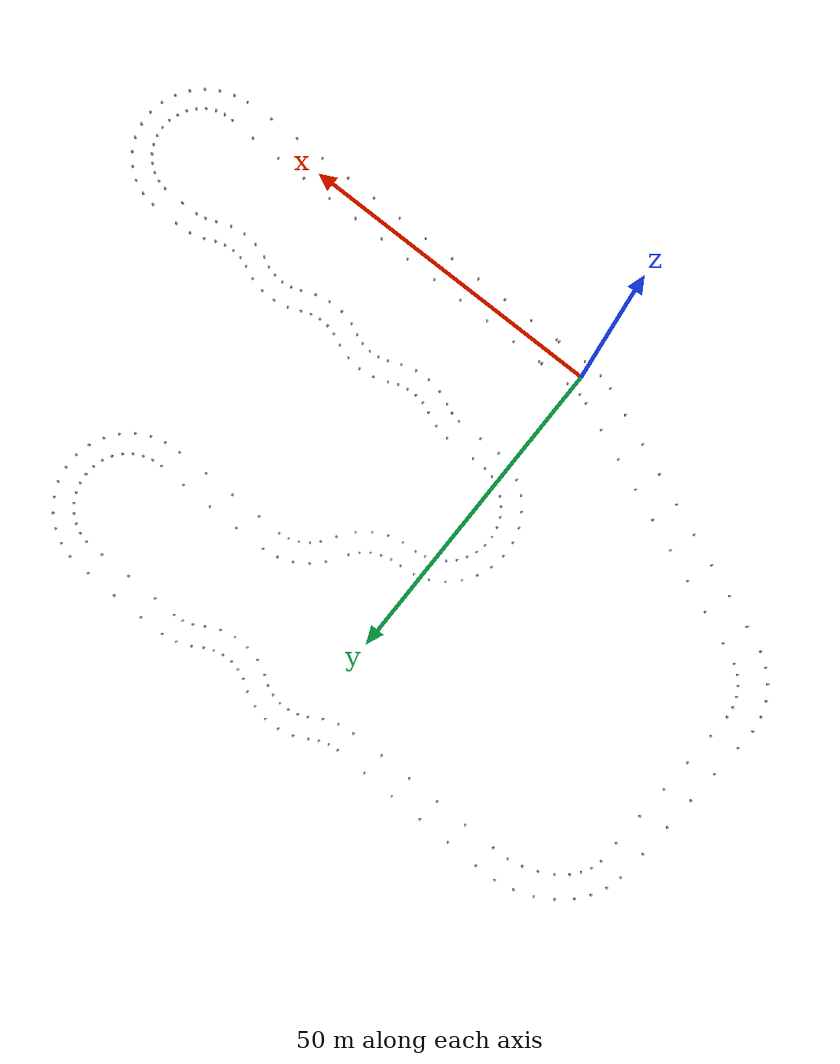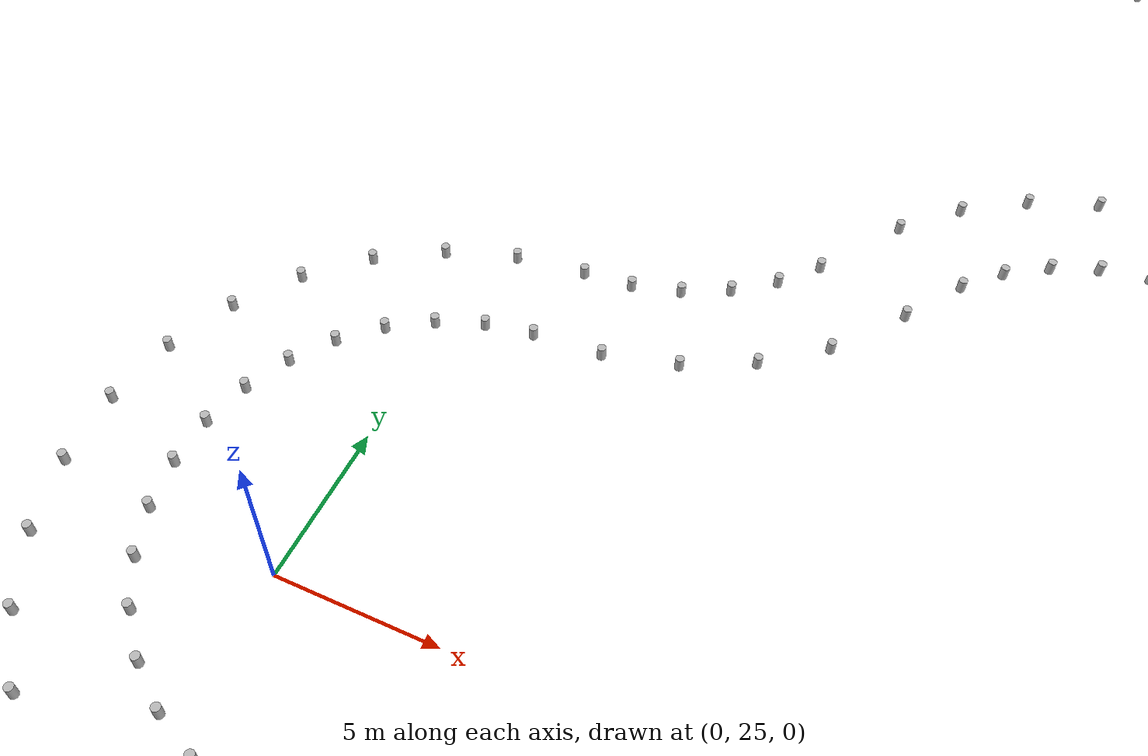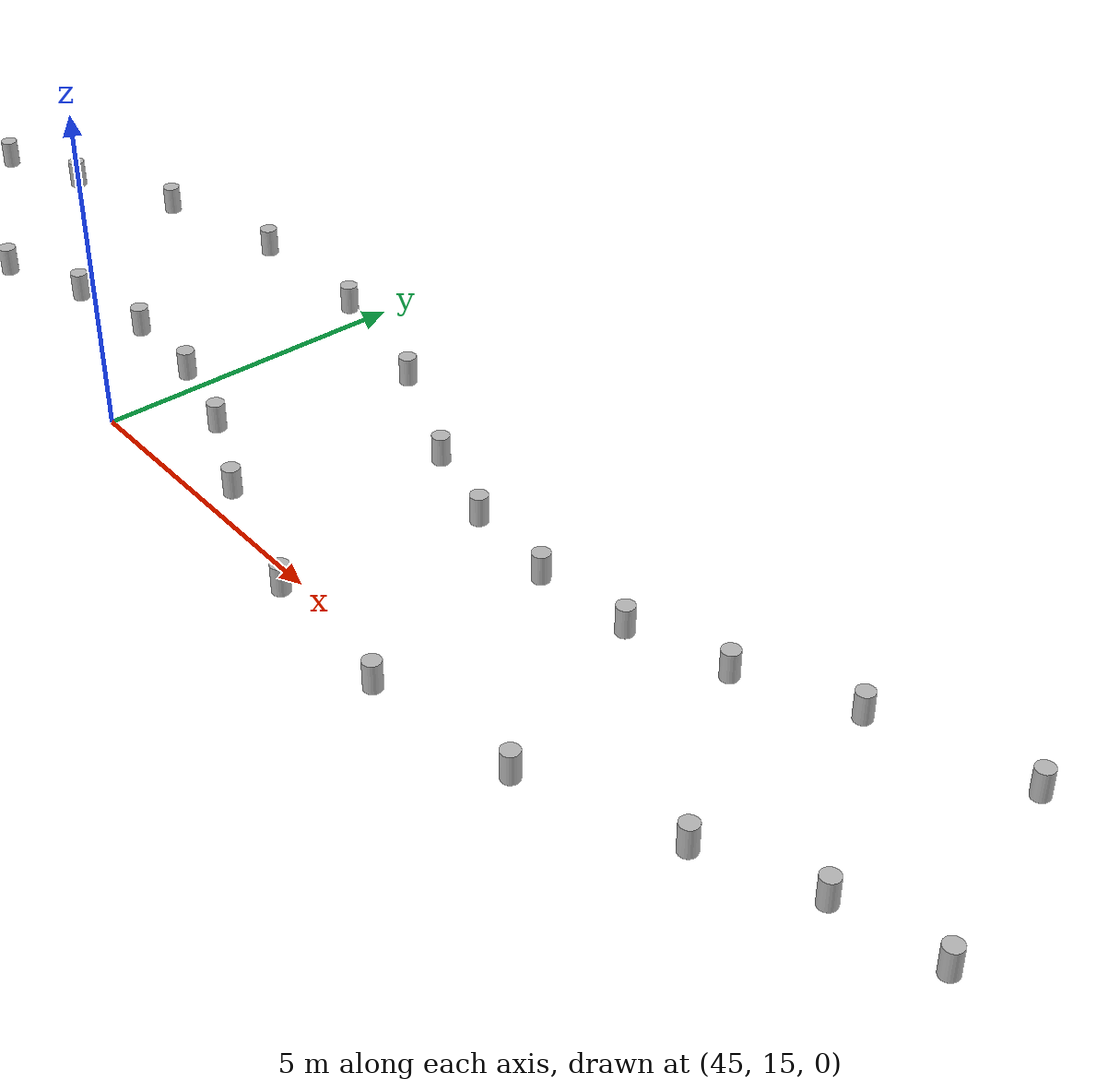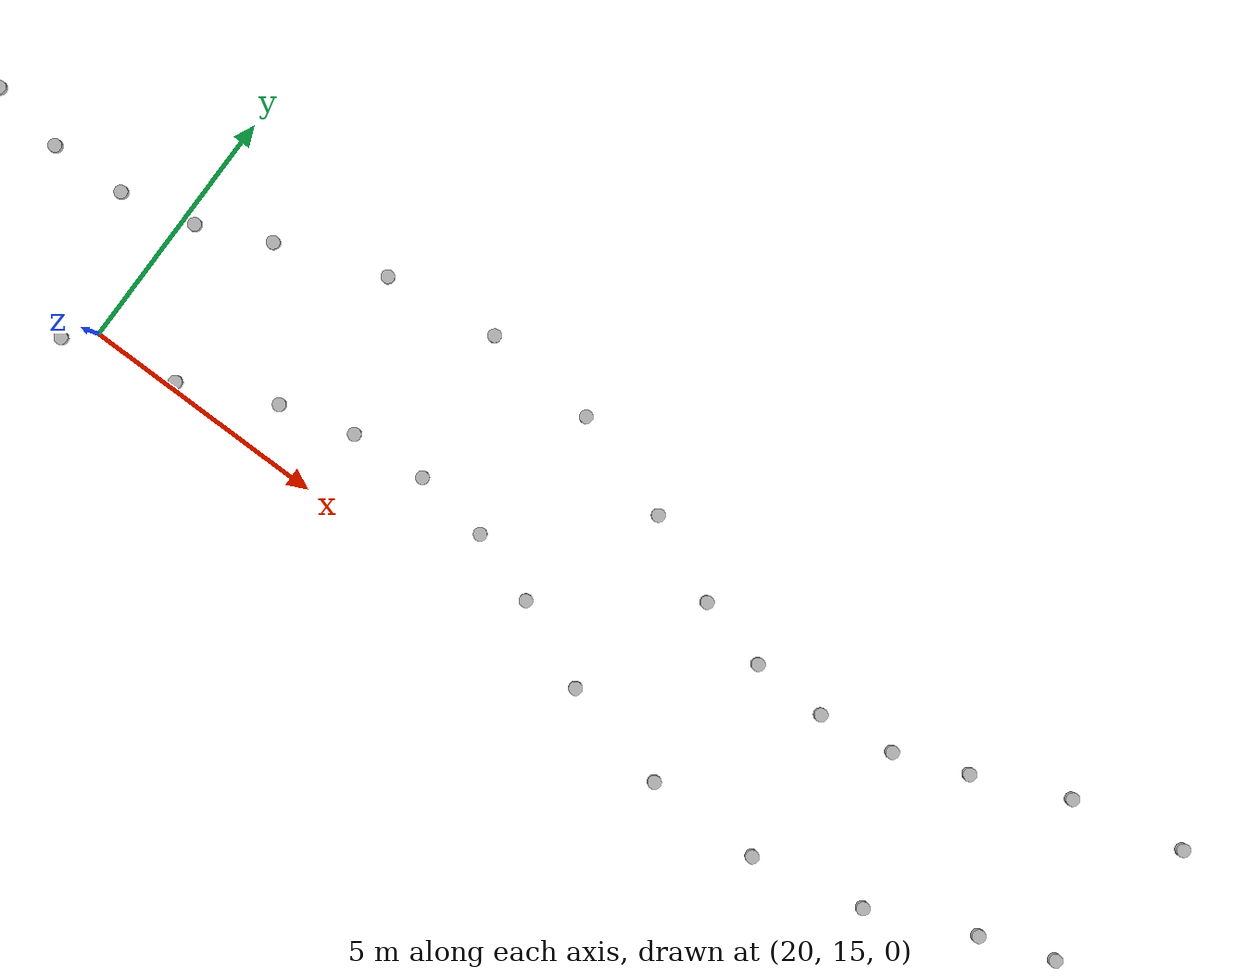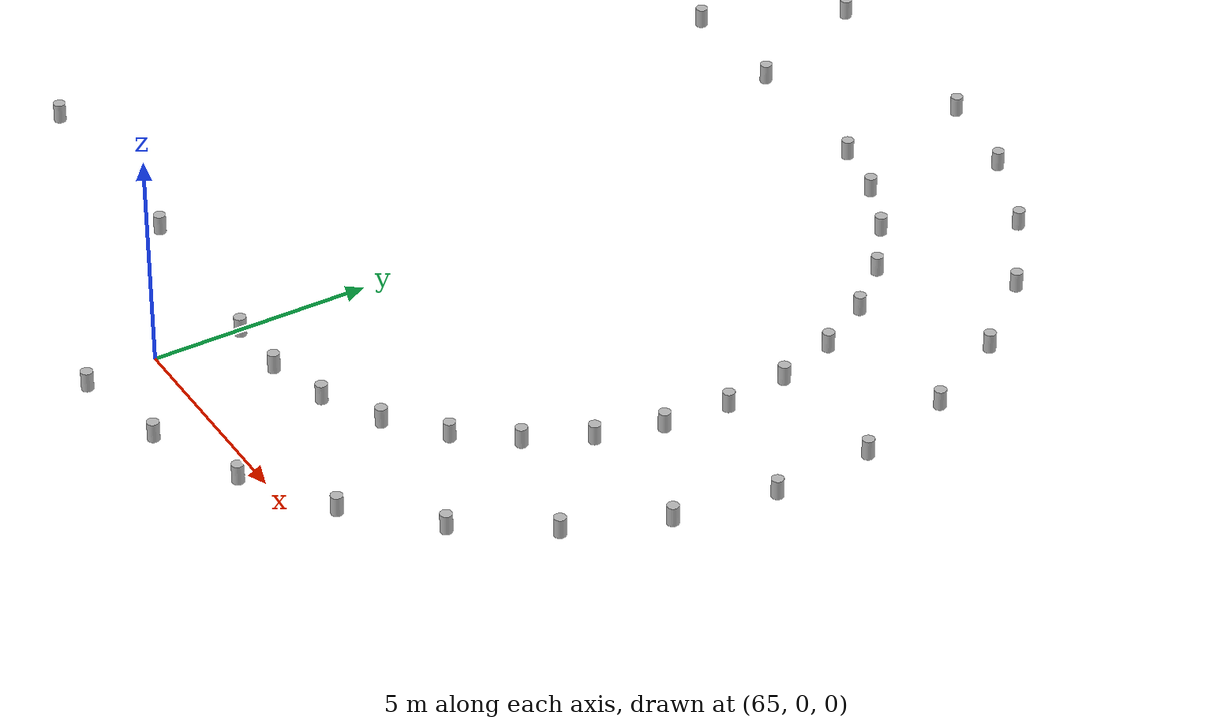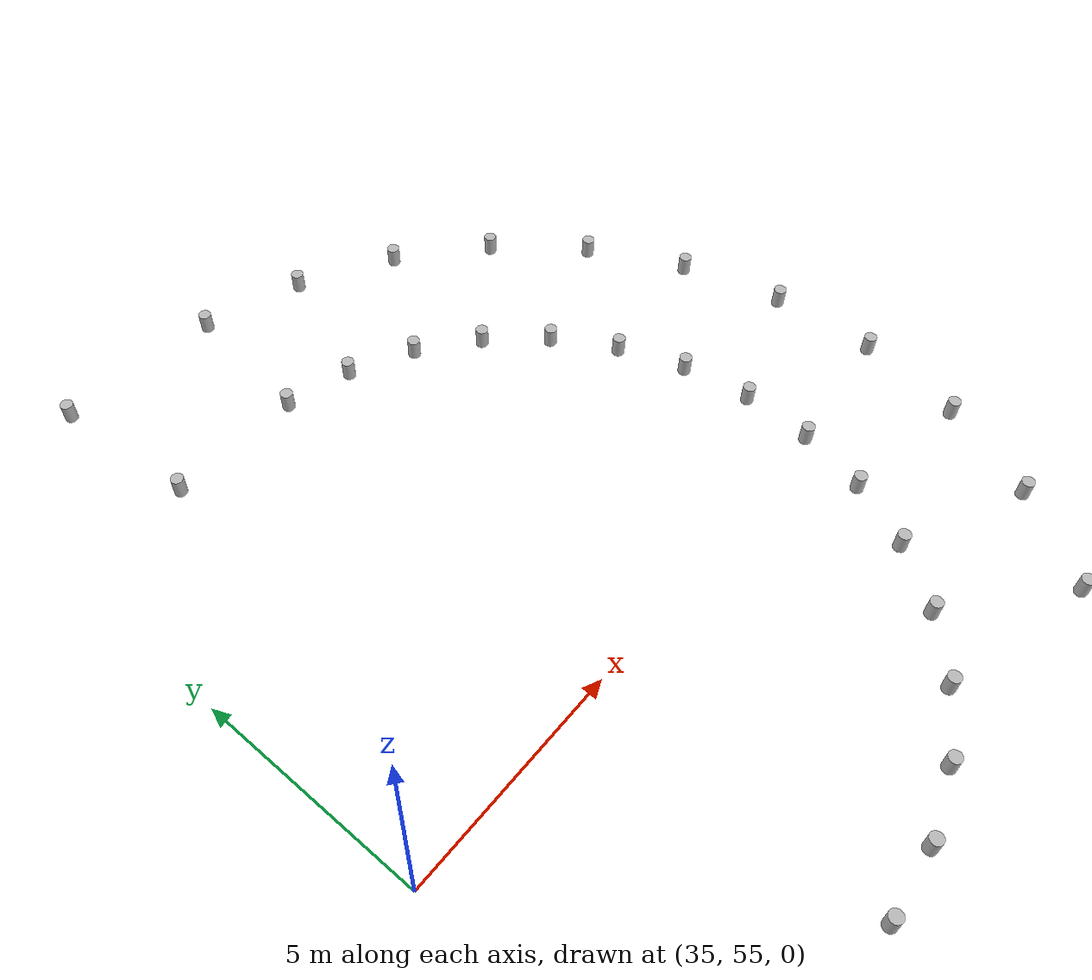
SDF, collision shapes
<?xml version='1.0'?>
<sdf version='1.6'>
  <model name='track'>

    <include>
      <pose>11.02 2.1 0.225 0 0 0</pose>
      <uri>model://blue_cone</uri>
      <name>blue_cone_0</name>

      <covariance x="0.01" y="0.01" xy="0.0"/>

    </include>

    <include>
      <pose>16.03 2.1 0.225 0 0 0</pose>
      <uri>model://blue_cone</uri>
      <name>blue_cone_1</name>

      <covariance x="0.01" y="0.01" xy="0.0"/>

    </include>

    <include>
      <pose>21.05 2.1 0.225 0 0 0</pose>
      <uri>model://blue_cone</uri>
      <name>blue_cone_2</name>

      <covariance x="0.01" y="0.01" xy="0.0"/>

    </include>

    <include>
      <pose>26.06 2.1 0.225 0 0 0</pose>
      <uri>model://blue_cone</uri>
      <name>blue_cone_3</name>

      <covariance x="0.01" y="0.01" xy="0.0"/>

    </include>

    <include>
      <pose>31.08 2.1 0.225 0 0 0</pose>
      <uri>model://blue_cone</uri>
      <name>blue_cone_4</name>

      <covariance x="0.01" y="0.01" xy="0.0"/>

    </include>

    <include>
      <pose>36.09 2.1 0.225 0 0 0</pose>
      <uri>model://blue_cone</uri>
      <name>blue_cone_5</name>

      <covariance x="0.01" y="0.01" xy="0.0"/>

    </include>

    <include>
      <pose>41.11 2.1 0.225 0 0 0</pose>
      <uri>model://blue_cone</uri>
      <name>blue_cone_6</name>

      <covariance x="0.01" y="0.01" xy="0.0"/>

    </include>

    <include>
      <pose>46.12 2.1 0.225 0 0 0</pose>
      <uri>model://blue_cone</uri>
      <name>blue_cone_7</name>

      <covariance x="0.01" y="0.01" xy="0.0"/>

    </include>

    <include>
      <pose>51.14 2.1 0.225 0 0 0</pose>
      <uri>model://blue_cone</uri>
      <name>blue_cone_8</name>

      <covariance x="0.01" y="0.01" xy="0.0"/>

    </include>

    <include>
      <pose>56.15 2.1 0.225 0 0 0</pose>
      <uri>model://blue_cone</uri>
      <name>blue_cone_9</name>

      <covariance x="0.01" y="0.01" xy="0.0"/>

    </include>

    <include>
      <pose>61.17 2.06 0.225 0 0 0</pose>
      <uri>model://blue_cone</uri>
      <name>blue_cone_10</name>

      <covariance x="0.01" y="0.01" xy="0.0"/>

    </include>

    <include>
      <pose>65.4 1.82 0.225 0 0 0</pose>
      <uri>model://blue_cone</uri>
      <name>blue_cone_11</name>

      <covariance x="0.01" y="0.01" xy="0.0"/>

    </include>

    <include>
      <pose>66.9 1.83 0.225 0 0 0</pose>
      <uri>model://blue_cone</uri>
      <name>blue_cone_12</name>

      <covariance x="0.01" y="0.01" xy="0.0"/>

    </include>

    <include>
      <pose>68.36 2.18 0.225 0 0 0</pose>
      <uri>model://blue_cone</uri>
      <name>blue_cone_13</name>

      <covariance x="0.01" y="0.01" xy="0.0"/>

    </include>

    <include>
      <pose>69.7 2.86 0.225 0 0 0</pose>
      <uri>model://blue_cone</uri>
      <name>blue_cone_14</name>

      <covariance x="0.01" y="0.01" xy="0.0"/>

    </include>

    <include>
      <pose>70.85 3.83 0.225 0 0 0</pose>
      <uri>model://blue_cone</uri>
      <name>blue_cone_15</name>

      <covariance x="0.01" y="0.01" xy="0.0"/>

    </include>

    <include>
      <pose>71.77 5.01 0.225 0 0 0</pose>
      <uri>model://blue_cone</uri>
      <name>blue_cone_16</name>

      <covariance x="0.01" y="0.01" xy="0.0"/>

    </include>

    <include>
      <pose>72.44 6.36 0.225 0 0 0</pose>
      <uri>model://blue_cone</uri>
      <name>blue_cone_17</name>

      <covariance x="0.01" y="0.01" xy="0.0"/>

    </include>

    <include>
      <pose>72.82 7.81 0.225 0 0 0</pose>
      <uri>model://blue_cone</uri>
      <name>blue_cone_18</name>

      <covariance x="0.01" y="0.01" xy="0.0"/>

    </include>

    <include>
      <pose>72.91 9.31 0.225 0 0 0</pose>
      <uri>model://blue_cone</uri>
      <name>blue_cone_19</name>

      <covariance x="0.01" y="0.01" xy="0.0"/>

    </include>

    <include>
      <pose>72.7 10.8 0.225 0 0 0</pose>
      <uri>model://blue_cone</uri>
      <name>blue_cone_20</name>

      <covariance x="0.01" y="0.01" xy="0.0"/>

    </include>

    <include>
      <pose>72.2 12.21 0.225 0 0 0</pose>
      <uri>model://blue_cone</uri>
      <name>blue_cone_21</name>

      <covariance x="0.01" y="0.01" xy="0.0"/>

    </include>

    <include>
      <pose>71.42 13.5 0.225 0 0 0</pose>
      <uri>model://blue_cone</uri>
      <name>blue_cone_22</name>

      <covariance x="0.01" y="0.01" xy="0.0"/>

    </include>

    <include>
      <pose>70.4 14.6 0.225 0 0 0</pose>
      <uri>model://blue_cone</uri>
      <name>blue_cone_23</name>

      <covariance x="0.01" y="0.01" xy="0.0"/>

    </include>

    <include>
      <pose>69.19 15.48 0.225 0 0 0</pose>
      <uri>model://blue_cone</uri>
      <name>blue_cone_24</name>

      <covariance x="0.01" y="0.01" xy="0.0"/>

    </include>

    <include>
      <pose>67.82 16.1 0.225 0 0 0</pose>
      <uri>model://blue_cone</uri>
      <name>blue_cone_25</name>

      <covariance x="0.01" y="0.01" xy="0.0"/>

    </include>

    <include>
      <pose>66.36 16.44 0.225 0 0 0</pose>
      <uri>model://blue_cone</uri>
      <name>blue_cone_26</name>

      <covariance x="0.01" y="0.01" xy="0.0"/>

    </include>

    <include>
      <pose>62.86 16.5 0.225 0 0 0</pose>
      <uri>model://blue_cone</uri>
      <name>blue_cone_27</name>

      <covariance x="0.01" y="0.01" xy="0.0"/>

    </include>

    <include>
      <pose>60.13 16.47 0.225 0 0 0</pose>
      <uri>model://blue_cone</uri>
      <name>blue_cone_28</name>

      <covariance x="0.01" y="0.01" xy="0.0"/>

    </include>

    <include>
      <pose>58.61 16.18 0.225 0 0 0</pose>
      <uri>model://blue_cone</uri>
      <name>blue_cone_29</name>

      <covariance x="0.01" y="0.01" xy="0.0"/>

    </include>

    <include>
      <pose>57.04 15.53 0.225 0 0 0</pose>
      <uri>model://blue_cone</uri>
      <name>blue_cone_30</name>

      <covariance x="0.01" y="0.01" xy="0.0"/>

    </include>

    <include>
      <pose>54.84 14.71 0.225 0 0 0</pose>
      <uri>model://blue_cone</uri>
      <name>blue_cone_31</name>

      <covariance x="0.01" y="0.01" xy="0.0"/>

    </include>

    <include>
      <pose>52.51 14.39 0.225 0 0 0</pose>
      <uri>model://blue_cone</uri>
      <name>blue_cone_32</name>

      <covariance x="0.01" y="0.01" xy="0.0"/>

    </include>

    <include>
      <pose>50.18 14.58 0.225 0 0 0</pose>
      <uri>model://blue_cone</uri>
      <name>blue_cone_33</name>

      <covariance x="0.01" y="0.01" xy="0.0"/>

    </include>

    <include>
      <pose>47.93 15.27 0.225 0 0 0</pose>
      <uri>model://blue_cone</uri>
      <name>blue_cone_34</name>

      <covariance x="0.01" y="0.01" xy="0.0"/>

    </include>

    <include>
      <pose>46.41 15.98 0.225 0 0 0</pose>
      <uri>model://blue_cone</uri>
      <name>blue_cone_35</name>

      <covariance x="0.01" y="0.01" xy="0.0"/>

    </include>

    <include>
      <pose>44.92 16.39 0.225 0 0 0</pose>
      <uri>model://blue_cone</uri>
      <name>blue_cone_36</name>

      <covariance x="0.01" y="0.01" xy="0.0"/>

    </include>

    <include>
      <pose>43.38 16.5 0.225 0 0 0</pose>
      <uri>model://blue_cone</uri>
      <name>blue_cone_37</name>

      <covariance x="0.01" y="0.01" xy="0.0"/>

    </include>

    <include>
      <pose>41.85 16.3 0.225 0 0 0</pose>
      <uri>model://blue_cone</uri>
      <name>blue_cone_38</name>

      <covariance x="0.01" y="0.01" xy="0.0"/>

    </include>

    <include>
      <pose>40.39 15.8 0.225 0 0 0</pose>
      <uri>model://blue_cone</uri>
      <name>blue_cone_39</name>

      <covariance x="0.01" y="0.01" xy="0.0"/>

    </include>

    <include>
      <pose>38.3 14.91 0.225 0 0 0</pose>
      <uri>model://blue_cone</uri>
      <name>blue_cone_40</name>

      <covariance x="0.01" y="0.01" xy="0.0"/>

    </include>

    <include>
      <pose>36.01 14.44 0.225 0 0 0</pose>
      <uri>model://blue_cone</uri>
      <name>blue_cone_41</name>

      <covariance x="0.01" y="0.01" xy="0.0"/>

    </include>

    <include>
      <pose>33.66 14.47 0.225 0 0 0</pose>
      <uri>model://blue_cone</uri>
      <name>blue_cone_42</name>

      <covariance x="0.01" y="0.01" xy="0.0"/>

    </include>

    <include>
      <pose>31.38 15.01 0.225 0 0 0</pose>
      <uri>model://blue_cone</uri>
      <name>blue_cone_43</name>

      <covariance x="0.01" y="0.01" xy="0.0"/>

    </include>

    <include>
      <pose>29.62 15.79 0.225 0 0 0</pose>
      <uri>model://blue_cone</uri>
      <name>blue_cone_44</name>

      <covariance x="0.01" y="0.01" xy="0.0"/>

    </include>

    <include>
      <pose>28.16 16.29 0.225 0 0 0</pose>
      <uri>model://blue_cone</uri>
      <name>blue_cone_45</name>

      <covariance x="0.01" y="0.01" xy="0.0"/>

    </include>

    <include>
      <pose>26.63 16.5 0.225 0 0 0</pose>
      <uri>model://blue_cone</uri>
      <name>blue_cone_46</name>

      <covariance x="0.01" y="0.01" xy="0.0"/>

    </include>

    <include>
      <pose>25.09 16.39 0.225 0 0 0</pose>
      <uri>model://blue_cone</uri>
      <name>blue_cone_47</name>

      <covariance x="0.01" y="0.01" xy="0.0"/>

    </include>

    <include>
      <pose>23.6 15.99 0.225 0 0 0</pose>
      <uri>model://blue_cone</uri>
      <name>blue_cone_48</name>

      <covariance x="0.01" y="0.01" xy="0.0"/>

    </include>

    <include>
      <pose>21.75 15.15 0.225 0 0 0</pose>
      <uri>model://blue_cone</uri>
      <name>blue_cone_49</name>

      <covariance x="0.01" y="0.01" xy="0.0"/>

    </include>

    <include>
      <pose>19.49 14.53 0.225 0 0 0</pose>
      <uri>model://blue_cone</uri>
      <name>blue_cone_50</name>

      <covariance x="0.01" y="0.01" xy="0.0"/>

    </include>

    <include>
      <pose>17.15 14.41 0.225 0 0 0</pose>
      <uri>model://blue_cone</uri>
      <name>blue_cone_51</name>

      <covariance x="0.01" y="0.01" xy="0.0"/>

    </include>

    <include>
      <pose>14.84 14.8 0.225 0 0 0</pose>
      <uri>model://blue_cone</uri>
      <name>blue_cone_52</name>

      <covariance x="0.01" y="0.01" xy="0.0"/>

    </include>

    <include>
      <pose>12.82 15.59 0.225 0 0 0</pose>
      <uri>model://blue_cone</uri>
      <name>blue_cone_53</name>

      <covariance x="0.01" y="0.01" xy="0.0"/>

    </include>

    <include>
      <pose>11.39 16.17 0.225 0 0 0</pose>
      <uri>model://blue_cone</uri>
      <name>blue_cone_54</name>

      <covariance x="0.01" y="0.01" xy="0.0"/>

    </include>

    <include>
      <pose>9.88 16.47 0.225 0 0 0</pose>
      <uri>model://blue_cone</uri>
      <name>blue_cone_55</name>

      <covariance x="0.01" y="0.01" xy="0.0"/>

    </include>

    <include>
      <pose>5.82 16.5 0.225 0 0 0</pose>
      <uri>model://blue_cone</uri>
      <name>blue_cone_56</name>

      <covariance x="0.01" y="0.01" xy="0.0"/>

    </include>

    <include>
      <pose>2.4 16.55 0.225 0 0 0</pose>
      <uri>model://blue_cone</uri>
      <name>blue_cone_57</name>

      <covariance x="0.01" y="0.01" xy="0.0"/>

    </include>

    <include>
      <pose>0.09 17.04 0.225 0 0 0</pose>
      <uri>model://blue_cone</uri>
      <name>blue_cone_58</name>

      <covariance x="0.01" y="0.01" xy="0.0"/>

    </include>

    <include>
      <pose>-2.06 18.01 0.225 0 0 0</pose>
      <uri>model://blue_cone</uri>
      <name>blue_cone_59</name>

      <covariance x="0.01" y="0.01" xy="0.0"/>

    </include>

    <include>
      <pose>-3.95 19.42 0.225 0 0 0</pose>
      <uri>model://blue_cone</uri>
      <name>blue_cone_60</name>

      <covariance x="0.01" y="0.01" xy="0.0"/>

    </include>

    <include>
      <pose>-5.49 21.2 0.225 0 0 0</pose>
      <uri>model://blue_cone</uri>
      <name>blue_cone_61</name>

      <covariance x="0.01" y="0.01" xy="0.0"/>

    </include>

    <include>
      <pose>-6.62 23.27 0.225 0 0 0</pose>
      <uri>model://blue_cone</uri>
      <name>blue_cone_62</name>

      <covariance x="0.01" y="0.01" xy="0.0"/>

    </include>

    <include>
      <pose>-7.27 25.53 0.225 0 0 0</pose>
      <uri>model://blue_cone</uri>
      <name>blue_cone_63</name>

      <covariance x="0.01" y="0.01" xy="0.0"/>

    </include>

    <include>
      <pose>-7.42 27.88 0.225 0 0 0</pose>
      <uri>model://blue_cone</uri>
      <name>blue_cone_64</name>

      <covariance x="0.01" y="0.01" xy="0.0"/>

    </include>

    <include>
      <pose>-7.06 30.21 0.225 0 0 0</pose>
      <uri>model://blue_cone</uri>
      <name>blue_cone_65</name>

      <covariance x="0.01" y="0.01" xy="0.0"/>

    </include>

    <include>
      <pose>-6.21 32.41 0.225 0 0 0</pose>
      <uri>model://blue_cone</uri>
      <name>blue_cone_66</name>

      <covariance x="0.01" y="0.01" xy="0.0"/>

    </include>

    <include>
      <pose>-4.9 34.37 0.225 0 0 0</pose>
      <uri>model://blue_cone</uri>
      <name>blue_cone_67</name>

      <covariance x="0.01" y="0.01" xy="0.0"/>

    </include>

    <include>
      <pose>-3.21 36.01 0.225 0 0 0</pose>
      <uri>model://blue_cone</uri>
      <name>blue_cone_68</name>

      <covariance x="0.01" y="0.01" xy="0.0"/>

    </include>

    <include>
      <pose>-1.2 37.25 0.225 0 0 0</pose>
      <uri>model://blue_cone</uri>
      <name>blue_cone_69</name>

      <covariance x="0.01" y="0.01" xy="0.0"/>

    </include>

    <include>
      <pose>1.02 38.02 0.225 0 0 0</pose>
      <uri>model://blue_cone</uri>
      <name>blue_cone_70</name>

      <covariance x="0.01" y="0.01" xy="0.0"/>

    </include>

    <include>
      <pose>3.27 38.3 0.225 0 0 0</pose>
      <uri>model://blue_cone</uri>
      <name>blue_cone_71</name>

      <covariance x="0.01" y="0.01" xy="0.0"/>

    </include>

    <include>
      <pose>4.85 38.42 0.225 0 0 0</pose>
      <uri>model://blue_cone</uri>
      <name>blue_cone_72</name>

      <covariance x="0.01" y="0.01" xy="0.0"/>

    </include>

    <include>
      <pose>6.37 38.84 0.225 0 0 0</pose>
      <uri>model://blue_cone</uri>
      <name>blue_cone_73</name>

      <covariance x="0.01" y="0.01" xy="0.0"/>

    </include>

    <include>
      <pose>7.79 39.55 0.225 0 0 0</pose>
      <uri>model://blue_cone</uri>
      <name>blue_cone_74</name>

      <covariance x="0.01" y="0.01" xy="0.0"/>

    </include>

    <include>
      <pose>9.04 40.52 0.225 0 0 0</pose>
      <uri>model://blue_cone</uri>
      <name>blue_cone_75</name>

      <covariance x="0.01" y="0.01" xy="0.0"/>

    </include>

    <include>
      <pose>10.08 41.72 0.225 0 0 0</pose>
      <uri>model://blue_cone</uri>
      <name>blue_cone_76</name>

      <covariance x="0.01" y="0.01" xy="0.0"/>

    </include>

    <include>
      <pose>11.97 44.53 0.225 0 0 0</pose>
      <uri>model://blue_cone</uri>
      <name>blue_cone_77</name>

      <covariance x="0.01" y="0.01" xy="0.0"/>

    </include>

    <include>
      <pose>13.64 46.22 0.225 0 0 0</pose>
      <uri>model://blue_cone</uri>
      <name>blue_cone_78</name>

      <covariance x="0.01" y="0.01" xy="0.0"/>

    </include>

    <include>
      <pose>15.62 47.53 0.225 0 0 0</pose>
      <uri>model://blue_cone</uri>
      <name>blue_cone_79</name>

      <covariance x="0.01" y="0.01" xy="0.0"/>

    </include>

    <include>
      <pose>17.84 48.41 0.225 0 0 0</pose>
      <uri>model://blue_cone</uri>
      <name>blue_cone_80</name>

      <covariance x="0.01" y="0.01" xy="0.0"/>

    </include>

    <include>
      <pose>20.18 48.81 0.225 0 0 0</pose>
      <uri>model://blue_cone</uri>
      <name>blue_cone_81</name>

      <covariance x="0.01" y="0.01" xy="0.0"/>

    </include>

    <include>
      <pose>25.09 48.92 0.225 0 0 0</pose>
      <uri>model://blue_cone</uri>
      <name>blue_cone_82</name>

      <covariance x="0.01" y="0.01" xy="0.0"/>

    </include>

    <include>
      <pose>30.11 48.94 0.225 0 0 0</pose>
      <uri>model://blue_cone</uri>
      <name>blue_cone_83</name>

      <covariance x="0.01" y="0.01" xy="0.0"/>

    </include>

    <include>
      <pose>35.12 48.92 0.225 0 0 0</pose>
      <uri>model://blue_cone</uri>
      <name>blue_cone_84</name>

      <covariance x="0.01" y="0.01" xy="0.0"/>

    </include>

    <include>
      <pose>39.44 48.84 0.225 0 0 0</pose>
      <uri>model://blue_cone</uri>
      <name>blue_cone_85</name>

      <covariance x="0.01" y="0.01" xy="0.0"/>

    </include>

    <include>
      <pose>40.96 48.94 0.225 0 0 0</pose>
      <uri>model://blue_cone</uri>
      <name>blue_cone_86</name>

      <covariance x="0.01" y="0.01" xy="0.0"/>

    </include>

    <include>
      <pose>42.43 49.36 0.225 0 0 0</pose>
      <uri>model://blue_cone</uri>
      <name>blue_cone_87</name>

      <covariance x="0.01" y="0.01" xy="0.0"/>

    </include>

    <include>
      <pose>43.79 50.07 0.225 0 0 0</pose>
      <uri>model://blue_cone</uri>
      <name>blue_cone_88</name>

      <covariance x="0.01" y="0.01" xy="0.0"/>

    </include>

    <include>
      <pose>44.97 51.04 0.225 0 0 0</pose>
      <uri>model://blue_cone</uri>
      <name>blue_cone_89</name>

      <covariance x="0.01" y="0.01" xy="0.0"/>

    </include>

    <include>
      <pose>45.93 52.23 0.225 0 0 0</pose>
      <uri>model://blue_cone</uri>
      <name>blue_cone_90</name>

      <covariance x="0.01" y="0.01" xy="0.0"/>

    </include>

    <include>
      <pose>46.63 53.59 0.225 0 0 0</pose>
      <uri>model://blue_cone</uri>
      <name>blue_cone_91</name>

      <covariance x="0.01" y="0.01" xy="0.0"/>

    </include>

    <include>
      <pose>47.05 55.06 0.225 0 0 0</pose>
      <uri>model://blue_cone</uri>
      <name>blue_cone_92</name>

      <covariance x="0.01" y="0.01" xy="0.0"/>

    </include>

    <include>
      <pose>47.17 56.59 0.225 0 0 0</pose>
      <uri>model://blue_cone</uri>
      <name>blue_cone_93</name>

      <covariance x="0.01" y="0.01" xy="0.0"/>

    </include>

    <include>
      <pose>46.99 58.11 0.225 0 0 0</pose>
      <uri>model://blue_cone</uri>
      <name>blue_cone_94</name>

      <covariance x="0.01" y="0.01" xy="0.0"/>

    </include>

    <include>
      <pose>46.51 59.56 0.225 0 0 0</pose>
      <uri>model://blue_cone</uri>
      <name>blue_cone_95</name>

      <covariance x="0.01" y="0.01" xy="0.0"/>

    </include>

    <include>
      <pose>45.76 60.89 0.225 0 0 0</pose>
      <uri>model://blue_cone</uri>
      <name>blue_cone_96</name>

      <covariance x="0.01" y="0.01" xy="0.0"/>

    </include>

    <include>
      <pose>44.75 62.04 0.225 0 0 0</pose>
      <uri>model://blue_cone</uri>
      <name>blue_cone_97</name>

      <covariance x="0.01" y="0.01" xy="0.0"/>

    </include>

    <include>
      <pose>43.53 62.97 0.225 0 0 0</pose>
      <uri>model://blue_cone</uri>
      <name>blue_cone_98</name>

      <covariance x="0.01" y="0.01" xy="0.0"/>

    </include>

    <include>
      <pose>42.15 63.63 0.225 0 0 0</pose>
      <uri>model://blue_cone</uri>
      <name>blue_cone_99</name>

      <covariance x="0.01" y="0.01" xy="0.0"/>

    </include>

    <include>
      <pose>40.67 63.98 0.225 0 0 0</pose>
      <uri>model://blue_cone</uri>
      <name>blue_cone_100</name>

      <covariance x="0.01" y="0.01" xy="0.0"/>

    </include>

    <include>
      <pose>37.71 64.0 0.225 0 0 0</pose>
      <uri>model://blue_cone</uri>
      <name>blue_cone_101</name>

      <covariance x="0.01" y="0.01" xy="0.0"/>

    </include>

    <include>
      <pose>32.7 63.94 0.225 0 0 0</pose>
      <uri>model://blue_cone</uri>
      <name>blue_cone_102</name>

      <covariance x="0.01" y="0.01" xy="0.0"/>

    </include>

    <include>
      <pose>27.68 63.96 0.225 0 0 0</pose>
      <uri>model://blue_cone</uri>
      <name>blue_cone_103</name>

      <covariance x="0.01" y="0.01" xy="0.0"/>

    </include>

    <include>
      <pose>24.01 64.04 0.225 0 0 0</pose>
      <uri>model://blue_cone</uri>
      <name>blue_cone_104</name>

      <covariance x="0.01" y="0.01" xy="0.0"/>

    </include>

    <include>
      <pose>22.51 63.88 0.225 0 0 0</pose>
      <uri>model://blue_cone</uri>
      <name>blue_cone_105</name>

      <covariance x="0.01" y="0.01" xy="0.0"/>

    </include>

    <include>
      <pose>21.08 63.42 0.225 0 0 0</pose>
      <uri>model://blue_cone</uri>
      <name>blue_cone_106</name>

      <covariance x="0.01" y="0.01" xy="0.0"/>

    </include>

    <include>
      <pose>19.55 62.53 0.225 0 0 0</pose>
      <uri>model://blue_cone</uri>
      <name>blue_cone_107</name>

      <covariance x="0.01" y="0.01" xy="0.0"/>

    </include>

    <include>
      <pose>17.47 61.53 0.225 0 0 0</pose>
      <uri>model://blue_cone</uri>
      <name>blue_cone_108</name>

      <covariance x="0.01" y="0.01" xy="0.0"/>

    </include>

    <include>
      <pose>15.22 61.01 0.225 0 0 0</pose>
      <uri>model://blue_cone</uri>
      <name>blue_cone_109</name>

      <covariance x="0.01" y="0.01" xy="0.0"/>

    </include>

    <include>
      <pose>12.91 60.99 0.225 0 0 0</pose>
      <uri>model://blue_cone</uri>
      <name>blue_cone_110</name>

      <covariance x="0.01" y="0.01" xy="0.0"/>

    </include>

    <include>
      <pose>10.65 61.48 0.225 0 0 0</pose>
      <uri>model://blue_cone</uri>
      <name>blue_cone_111</name>

      <covariance x="0.01" y="0.01" xy="0.0"/>

    </include>

    <include>
      <pose>8.55 62.45 0.225 0 0 0</pose>
      <uri>model://blue_cone</uri>
      <name>blue_cone_112</name>

      <covariance x="0.01" y="0.01" xy="0.0"/>

    </include>

    <include>
      <pose>7.2 63.29 0.225 0 0 0</pose>
      <uri>model://blue_cone</uri>
      <name>blue_cone_113</name>

      <covariance x="0.01" y="0.01" xy="0.0"/>

    </include>

    <include>
      <pose>5.8 63.84 0.225 0 0 0</pose>
      <uri>model://blue_cone</uri>
      <name>blue_cone_114</name>

      <covariance x="0.01" y="0.01" xy="0.0"/>

    </include>

    <include>
      <pose>4.33 64.11 0.225 0 0 0</pose>
      <uri>model://blue_cone</uri>
      <name>blue_cone_115</name>

      <covariance x="0.01" y="0.01" xy="0.0"/>

    </include>

    <include>
      <pose>2.82 64.08 0.225 0 0 0</pose>
      <uri>model://blue_cone</uri>
      <name>blue_cone_116</name>

      <covariance x="0.01" y="0.01" xy="0.0"/>

    </include>

    <include>
      <pose>1.36 63.75 0.225 0 0 0</pose>
      <uri>model://blue_cone</uri>
      <name>blue_cone_117</name>

      <covariance x="0.01" y="0.01" xy="0.0"/>

    </include>

    <include>
      <pose>-0.01 63.13 0.225 0 0 0</pose>
      <uri>model://blue_cone</uri>
      <name>blue_cone_118</name>

      <covariance x="0.01" y="0.01" xy="0.0"/>

    </include>

    <include>
      <pose>-1.83 62.02 0.225 0 0 0</pose>
      <uri>model://blue_cone</uri>
      <name>blue_cone_119</name>

      <covariance x="0.01" y="0.01" xy="0.0"/>

    </include>

    <include>
      <pose>-3.99 61.2 0.225 0 0 0</pose>
      <uri>model://blue_cone</uri>
      <name>blue_cone_120</name>

      <covariance x="0.01" y="0.01" xy="0.0"/>

    </include>

    <include>
      <pose>-6.46 60.84 0.225 0 0 0</pose>
      <uri>model://blue_cone</uri>
      <name>blue_cone_121</name>

      <covariance x="0.01" y="0.01" xy="0.0"/>

    </include>

    <include>
      <pose>-11.47 60.74 0.225 0 0 0</pose>
      <uri>model://blue_cone</uri>
      <name>blue_cone_122</name>

      <covariance x="0.01" y="0.01" xy="0.0"/>

    </include>

    <include>
      <pose>-16.49 60.73 0.225 0 0 0</pose>
      <uri>model://blue_cone</uri>
      <name>blue_cone_123</name>

      <covariance x="0.01" y="0.01" xy="0.0"/>

    </include>

    <include>
      <pose>-21.5 60.73 0.225 0 0 0</pose>
      <uri>model://blue_cone</uri>
      <name>blue_cone_124</name>

      <covariance x="0.01" y="0.01" xy="0.0"/>

    </include>

    <include>
      <pose>-26.52 60.73 0.225 0 0 0</pose>
      <uri>model://blue_cone</uri>
      <name>blue_cone_125</name>

      <covariance x="0.01" y="0.01" xy="0.0"/>

    </include>

    <include>
      <pose>-31.53 60.73 0.225 0 0 0</pose>
      <uri>model://blue_cone</uri>
      <name>blue_cone_126</name>

      <covariance x="0.01" y="0.01" xy="0.0"/>

    </include>

    <include>
      <pose>-33.96 60.62 0.225 0 0 0</pose>
      <uri>model://blue_cone</uri>
      <name>blue_cone_127</name>

      <covariance x="0.01" y="0.01" xy="0.0"/>

    </include>

    <include>
      <pose>-36.2 60.14 0.225 0 0 0</pose>
      <uri>model://blue_cone</uri>
      <name>blue_cone_128</name>

      <covariance x="0.01" y="0.01" xy="0.0"/>

    </include>

    <include>
      <pose>-38.34 59.33 0.225 0 0 0</pose>
      <uri>model://blue_cone</uri>
      <name>blue_cone_129</name>

      <covariance x="0.01" y="0.01" xy="0.0"/>

    </include>

    <include>
      <pose>-40.32 58.19 0.225 0 0 0</pose>
      <uri>model://blue_cone</uri>
      <name>blue_cone_130</name>

      <covariance x="0.01" y="0.01" xy="0.0"/>

    </include>

    <include>
      <pose>-41.99 56.87 0.225 0 0 0</pose>
      <uri>model://blue_cone</uri>
      <name>blue_cone_131</name>

      <covariance x="0.01" y="0.01" xy="0.0"/>

    </include>

    <include>
      <pose>-43.05 55.67 0.225 0 0 0</pose>
      <uri>model://blue_cone</uri>
      <name>blue_cone_132</name>

      <covariance x="0.01" y="0.01" xy="0.0"/>

    </include>

    <include>
      <pose>-43.82 54.27 0.225 0 0 0</pose>
      <uri>model://blue_cone</uri>
      <name>blue_cone_133</name>

      <covariance x="0.01" y="0.01" xy="0.0"/>

    </include>

    <include>
      <pose>-44.28 52.73 0.225 0 0 0</pose>
      <uri>model://blue_cone</uri>
      <name>blue_cone_134</name>

      <covariance x="0.01" y="0.01" xy="0.0"/>

    </include>

    <include>
      <pose>-44.48 49.48 0.225 0 0 0</pose>
      <uri>model://blue_cone</uri>
      <name>blue_cone_135</name>

      <covariance x="0.01" y="0.01" xy="0.0"/>

    </include>

    <include>
      <pose>-44.79 44.47 0.225 0 0 0</pose>
      <uri>model://blue_cone</uri>
      <name>blue_cone_136</name>

      <covariance x="0.01" y="0.01" xy="0.0"/>

    </include>

    <include>
      <pose>-45.18 39.47 0.225 0 0 0</pose>
      <uri>model://blue_cone</uri>
      <name>blue_cone_137</name>

      <covariance x="0.01" y="0.01" xy="0.0"/>

    </include>

    <include>
      <pose>-45.56 34.47 0.225 0 0 0</pose>
      <uri>model://blue_cone</uri>
      <name>blue_cone_138</name>

      <covariance x="0.01" y="0.01" xy="0.0"/>

    </include>

    <include>
      <pose>-45.92 29.47 0.225 0 0 0</pose>
      <uri>model://blue_cone</uri>
      <name>blue_cone_139</name>

      <covariance x="0.01" y="0.01" xy="0.0"/>

    </include>

    <include>
      <pose>-46.11 25.91 0.225 0 0 0</pose>
      <uri>model://blue_cone</uri>
      <name>blue_cone_140</name>

      <covariance x="0.01" y="0.01" xy="0.0"/>

    </include>

    <include>
      <pose>-45.95 24.35 0.225 0 0 0</pose>
      <uri>model://blue_cone</uri>
      <name>blue_cone_141</name>

      <covariance x="0.01" y="0.01" xy="0.0"/>

    </include>

    <include>
      <pose>-45.48 22.84 0.225 0 0 0</pose>
      <uri>model://blue_cone</uri>
      <name>blue_cone_142</name>

      <covariance x="0.01" y="0.01" xy="0.0"/>

    </include>

    <include>
      <pose>-44.72 21.46 0.225 0 0 0</pose>
      <uri>model://blue_cone</uri>
      <name>blue_cone_143</name>

      <covariance x="0.01" y="0.01" xy="0.0"/>

    </include>

    <include>
      <pose>-43.69 20.27 0.225 0 0 0</pose>
      <uri>model://blue_cone</uri>
      <name>blue_cone_144</name>

      <covariance x="0.01" y="0.01" xy="0.0"/>

    </include>

    <include>
      <pose>-42.44 19.31 0.225 0 0 0</pose>
      <uri>model://blue_cone</uri>
      <name>blue_cone_145</name>

      <covariance x="0.01" y="0.01" xy="0.0"/>

    </include>

    <include>
      <pose>-39.46 17.98 0.225 0 0 0</pose>
      <uri>model://blue_cone</uri>
      <name>blue_cone_146</name>

      <covariance x="0.01" y="0.01" xy="0.0"/>

    </include>

    <include>
      <pose>-34.83 16.05 0.225 0 0 0</pose>
      <uri>model://blue_cone</uri>
      <name>blue_cone_147</name>

      <covariance x="0.01" y="0.01" xy="0.0"/>

    </include>

    <include>
      <pose>-30.21 14.11 0.225 0 0 0</pose>
      <uri>model://blue_cone</uri>
      <name>blue_cone_148</name>

      <covariance x="0.01" y="0.01" xy="0.0"/>

    </include>

    <include>
      <pose>-25.58 12.18 0.225 0 0 0</pose>
      <uri>model://blue_cone</uri>
      <name>blue_cone_149</name>

      <covariance x="0.01" y="0.01" xy="0.0"/>

    </include>

    <include>
      <pose>-20.95 10.24 0.225 0 0 0</pose>
      <uri>model://blue_cone</uri>
      <name>blue_cone_150</name>

      <covariance x="0.01" y="0.01" xy="0.0"/>

    </include>

    <include>
      <pose>-16.33 8.31 0.225 0 0 0</pose>
      <uri>model://blue_cone</uri>
      <name>blue_cone_151</name>

      <covariance x="0.01" y="0.01" xy="0.0"/>

    </include>

    <include>
      <pose>-11.7 6.37 0.225 0 0 0</pose>
      <uri>model://blue_cone</uri>
      <name>blue_cone_152</name>

      <covariance x="0.01" y="0.01" xy="0.0"/>

    </include>

    <include>
      <pose>-7.07 4.44 0.225 0 0 0</pose>
      <uri>model://blue_cone</uri>
      <name>blue_cone_153</name>

      <covariance x="0.01" y="0.01" xy="0.0"/>

    </include>

    <include>
      <pose>-2.95 2.71 0.225 0 0 0</pose>
      <uri>model://blue_cone</uri>
      <name>blue_cone_154</name>

      <covariance x="0.01" y="0.01" xy="0.0"/>

    </include>

    <include>
      <pose>-1.44 2.24 0.225 0 0 0</pose>
      <uri>model://blue_cone</uri>
      <name>blue_cone_155</name>

      <covariance x="0.01" y="0.01" xy="0.0"/>

    </include>

    <include>
      <pose>0.98 2.1 0.225 0 0 0</pose>
      <uri>model://blue_cone</uri>
      <name>blue_cone_156</name>

      <covariance x="0.01" y="0.01" xy="0.0"/>

    </include>

    <include>
      <pose>11.0 -2.1 0.225 0 0 0</pose>
      <uri>model://yellow_cone</uri>
      <name>yellow_cone_157</name>

      <covariance x="0.01" y="0.01" xy="0.0"/>

    </include>

    <include>
      <pose>15.99 -2.1 0.225 0 0 0</pose>
      <uri>model://yellow_cone</uri>
      <name>yellow_cone_158</name>

      <covariance x="0.01" y="0.01" xy="0.0"/>

    </include>

    <include>
      <pose>20.99 -2.1 0.225 0 0 0</pose>
      <uri>model://yellow_cone</uri>
      <name>yellow_cone_159</name>

      <covariance x="0.01" y="0.01" xy="0.0"/>

    </include>

    <include>
      <pose>25.99 -2.1 0.225 0 0 0</pose>
      <uri>model://yellow_cone</uri>
      <name>yellow_cone_160</name>

      <covariance x="0.01" y="0.01" xy="0.0"/>

    </include>

    <include>
      <pose>30.99 -2.1 0.225 0 0 0</pose>
      <uri>model://yellow_cone</uri>
      <name>yellow_cone_161</name>

      <covariance x="0.01" y="0.01" xy="0.0"/>

    </include>

    <include>
      <pose>35.98 -2.1 0.225 0 0 0</pose>
      <uri>model://yellow_cone</uri>
      <name>yellow_cone_162</name>

      <covariance x="0.01" y="0.01" xy="0.0"/>

    </include>

    <include>
      <pose>40.98 -2.1 0.225 0 0 0</pose>
      <uri>model://yellow_cone</uri>
      <name>yellow_cone_163</name>

      <covariance x="0.01" y="0.01" xy="0.0"/>

    </include>

    <include>
      <pose>45.98 -2.1 0.225 0 0 0</pose>
      <uri>model://yellow_cone</uri>
      <name>yellow_cone_164</name>

      <covariance x="0.01" y="0.01" xy="0.0"/>

    </include>

    <include>
      <pose>50.97 -2.1 0.225 0 0 0</pose>
      <uri>model://yellow_cone</uri>
      <name>yellow_cone_165</name>

      <covariance x="0.01" y="0.01" xy="0.0"/>

    </include>

    <include>
      <pose>55.97 -2.1 0.225 0 0 0</pose>
      <uri>model://yellow_cone</uri>
      <name>yellow_cone_166</name>

      <covariance x="0.01" y="0.01" xy="0.0"/>

    </include>

    <include>
      <pose>60.97 -2.07 0.225 0 0 0</pose>
      <uri>model://yellow_cone</uri>
      <name>yellow_cone_167</name>

      <covariance x="0.01" y="0.01" xy="0.0"/>

    </include>

    <include>
      <pose>65.48 -1.81 0.225 0 0 0</pose>
      <uri>model://yellow_cone</uri>
      <name>yellow_cone_168</name>

      <covariance x="0.01" y="0.01" xy="0.0"/>

    </include>

    <include>
      <pose>67.74 -1.41 0.225 0 0 0</pose>
      <uri>model://yellow_cone</uri>
      <name>yellow_cone_169</name>

      <covariance x="0.01" y="0.01" xy="0.0"/>

    </include>

    <include>
      <pose>69.89 -0.57 0.225 0 0 0</pose>
      <uri>model://yellow_cone</uri>
      <name>yellow_cone_170</name>

      <covariance x="0.01" y="0.01" xy="0.0"/>

    </include>

    <include>
      <pose>71.83 0.67 0.225 0 0 0</pose>
      <uri>model://yellow_cone</uri>
      <name>yellow_cone_171</name>

      <covariance x="0.01" y="0.01" xy="0.0"/>

    </include>

    <include>
      <pose>73.48 2.28 0.225 0 0 0</pose>
      <uri>model://yellow_cone</uri>
      <name>yellow_cone_172</name>

      <covariance x="0.01" y="0.01" xy="0.0"/>

    </include>

    <include>
      <pose>74.75 4.19 0.225 0 0 0</pose>
      <uri>model://yellow_cone</uri>
      <name>yellow_cone_173</name>

      <covariance x="0.01" y="0.01" xy="0.0"/>

    </include>

    <include>
      <pose>75.58 6.34 0.225 0 0 0</pose>
      <uri>model://yellow_cone</uri>
      <name>yellow_cone_174</name>

      <covariance x="0.01" y="0.01" xy="0.0"/>

    </include>

    <include>
      <pose>75.91 8.62 0.225 0 0 0</pose>
      <uri>model://yellow_cone</uri>
      <name>yellow_cone_175</name>

      <covariance x="0.01" y="0.01" xy="0.0"/>

    </include>

    <include>
      <pose>75.74 10.92 0.225 0 0 0</pose>
      <uri>model://yellow_cone</uri>
      <name>yellow_cone_176</name>

      <covariance x="0.01" y="0.01" xy="0.0"/>

    </include>

    <include>
      <pose>75.08 13.12 0.225 0 0 0</pose>
      <uri>model://yellow_cone</uri>
      <name>yellow_cone_177</name>

      <covariance x="0.01" y="0.01" xy="0.0"/>

    </include>

    <include>
      <pose>73.95 15.12 0.225 0 0 0</pose>
      <uri>model://yellow_cone</uri>
      <name>yellow_cone_178</name>

      <covariance x="0.01" y="0.01" xy="0.0"/>

    </include>

    <include>
      <pose>72.41 16.84 0.225 0 0 0</pose>
      <uri>model://yellow_cone</uri>
      <name>yellow_cone_179</name>

      <covariance x="0.01" y="0.01" xy="0.0"/>

    </include>

    <include>
      <pose>70.53 18.17 0.225 0 0 0</pose>
      <uri>model://yellow_cone</uri>
      <name>yellow_cone_180</name>

      <covariance x="0.01" y="0.01" xy="0.0"/>

    </include>

    <include>
      <pose>68.41 19.06 0.225 0 0 0</pose>
      <uri>model://yellow_cone</uri>
      <name>yellow_cone_181</name>

      <covariance x="0.01" y="0.01" xy="0.0"/>

    </include>

    <include>
      <pose>66.15 19.47 0.225 0 0 0</pose>
      <uri>model://yellow_cone</uri>
      <name>yellow_cone_182</name>

      <covariance x="0.01" y="0.01" xy="0.0"/>

    </include>

    <include>
      <pose>61.52 19.5 0.225 0 0 0</pose>
      <uri>model://yellow_cone</uri>
      <name>yellow_cone_183</name>

      <covariance x="0.01" y="0.01" xy="0.0"/>

    </include>

    <include>
      <pose>58.99 19.34 0.225 0 0 0</pose>
      <uri>model://yellow_cone</uri>
      <name>yellow_cone_184</name>

      <covariance x="0.01" y="0.01" xy="0.0"/>

    </include>

    <include>
      <pose>56.75 18.7 0.225 0 0 0</pose>
      <uri>model://yellow_cone</uri>
      <name>yellow_cone_185</name>

      <covariance x="0.01" y="0.01" xy="0.0"/>

    </include>

    <include>
      <pose>55.16 17.97 0.225 0 0 0</pose>
      <uri>model://yellow_cone</uri>
      <name>yellow_cone_186</name>

      <covariance x="0.01" y="0.01" xy="0.0"/>

    </include>

    <include>
      <pose>53.68 17.53 0.225 0 0 0</pose>
      <uri>model://yellow_cone</uri>
      <name>yellow_cone_187</name>

      <covariance x="0.01" y="0.01" xy="0.0"/>

    </include>

    <include>
      <pose>52.15 17.39 0.225 0 0 0</pose>
      <uri>model://yellow_cone</uri>
      <name>yellow_cone_188</name>

      <covariance x="0.01" y="0.01" xy="0.0"/>

    </include>

    <include>
      <pose>50.62 17.55 0.225 0 0 0</pose>
      <uri>model://yellow_cone</uri>
      <name>yellow_cone_189</name>

      <covariance x="0.01" y="0.01" xy="0.0"/>

    </include>

    <include>
      <pose>49.15 18.01 0.225 0 0 0</pose>
      <uri>model://yellow_cone</uri>
      <name>yellow_cone_190</name>

      <covariance x="0.01" y="0.01" xy="0.0"/>

    </include>

    <include>
      <pose>47.17 18.89 0.225 0 0 0</pose>
      <uri>model://yellow_cone</uri>
      <name>yellow_cone_191</name>

      <covariance x="0.01" y="0.01" xy="0.0"/>

    </include>

    <include>
      <pose>44.89 19.42 0.225 0 0 0</pose>
      <uri>model://yellow_cone</uri>
      <name>yellow_cone_192</name>

      <covariance x="0.01" y="0.01" xy="0.0"/>

    </include>

    <include>
      <pose>42.55 19.45 0.225 0 0 0</pose>
      <uri>model://yellow_cone</uri>
      <name>yellow_cone_193</name>

      <covariance x="0.01" y="0.01" xy="0.0"/>

    </include>

    <include>
      <pose>40.27 18.97 0.225 0 0 0</pose>
      <uri>model://yellow_cone</uri>
      <name>yellow_cone_194</name>

      <covariance x="0.01" y="0.01" xy="0.0"/>

    </include>

    <include>
      <pose>38.41 18.18 0.225 0 0 0</pose>
      <uri>model://yellow_cone</uri>
      <name>yellow_cone_195</name>

      <covariance x="0.01" y="0.01" xy="0.0"/>

    </include>

    <include>
      <pose>36.97 17.64 0.225 0 0 0</pose>
      <uri>model://yellow_cone</uri>
      <name>yellow_cone_196</name>

      <covariance x="0.01" y="0.01" xy="0.0"/>

    </include>

    <include>
      <pose>35.45 17.4 0.225 0 0 0</pose>
      <uri>model://yellow_cone</uri>
      <name>yellow_cone_197</name>

      <covariance x="0.01" y="0.01" xy="0.0"/>

    </include>

    <include>
      <pose>33.91 17.46 0.225 0 0 0</pose>
      <uri>model://yellow_cone</uri>
      <name>yellow_cone_198</name>

      <covariance x="0.01" y="0.01" xy="0.0"/>

    </include>

    <include>
      <pose>32.42 17.83 0.225 0 0 0</pose>
      <uri>model://yellow_cone</uri>
      <name>yellow_cone_199</name>

      <covariance x="0.01" y="0.01" xy="0.0"/>

    </include>

    <include>
      <pose>30.68 18.61 0.225 0 0 0</pose>
      <uri>model://yellow_cone</uri>
      <name>yellow_cone_200</name>

      <covariance x="0.01" y="0.01" xy="0.0"/>

    </include>

    <include>
      <pose>28.45 19.3 0.225 0 0 0</pose>
      <uri>model://yellow_cone</uri>
      <name>yellow_cone_201</name>

      <covariance x="0.01" y="0.01" xy="0.0"/>

    </include>

    <include>
      <pose>26.12 19.5 0.225 0 0 0</pose>
      <uri>model://yellow_cone</uri>
      <name>yellow_cone_202</name>

      <covariance x="0.01" y="0.01" xy="0.0"/>

    </include>

    <include>
      <pose>23.81 19.19 0.225 0 0 0</pose>
      <uri>model://yellow_cone</uri>
      <name>yellow_cone_203</name>

      <covariance x="0.01" y="0.01" xy="0.0"/>

    </include>

    <include>
      <pose>21.66 18.41 0.225 0 0 0</pose>
      <uri>model://yellow_cone</uri>
      <name>yellow_cone_204</name>

      <covariance x="0.01" y="0.01" xy="0.0"/>

    </include>

    <include>
      <pose>20.25 17.79 0.225 0 0 0</pose>
      <uri>model://yellow_cone</uri>
      <name>yellow_cone_205</name>

      <covariance x="0.01" y="0.01" xy="0.0"/>

    </include>

    <include>
      <pose>18.75 17.45 0.225 0 0 0</pose>
      <uri>model://yellow_cone</uri>
      <name>yellow_cone_206</name>

      <covariance x="0.01" y="0.01" xy="0.0"/>

    </include>

    <include>
      <pose>17.21 17.41 0.225 0 0 0</pose>
      <uri>model://yellow_cone</uri>
      <name>yellow_cone_207</name>

      <covariance x="0.01" y="0.01" xy="0.0"/>

    </include>

    <include>
      <pose>15.69 17.67 0.225 0 0 0</pose>
      <uri>model://yellow_cone</uri>
      <name>yellow_cone_208</name>

      <covariance x="0.01" y="0.01" xy="0.0"/>

    </include>

    <include>
      <pose>14.17 18.27 0.225 0 0 0</pose>
      <uri>model://yellow_cone</uri>
      <name>yellow_cone_209</name>

      <covariance x="0.01" y="0.01" xy="0.0"/>

    </include>

    <include>
      <pose>12.0 19.12 0.225 0 0 0</pose>
      <uri>model://yellow_cone</uri>
      <name>yellow_cone_210</name>

      <covariance x="0.01" y="0.01" xy="0.0"/>

    </include>

    <include>
      <pose>9.69 19.49 0.225 0 0 0</pose>
      <uri>model://yellow_cone</uri>
      <name>yellow_cone_211</name>

      <covariance x="0.01" y="0.01" xy="0.0"/>

    </include>

    <include>
      <pose>4.84 19.5 0.225 0 0 0</pose>
      <uri>model://yellow_cone</uri>
      <name>yellow_cone_212</name>

      <covariance x="0.01" y="0.01" xy="0.0"/>

    </include>

    <include>
      <pose>2.57 19.55 0.225 0 0 0</pose>
      <uri>model://yellow_cone</uri>
      <name>yellow_cone_213</name>

      <covariance x="0.01" y="0.01" xy="0.0"/>

    </include>

    <include>
      <pose>1.06 19.88 0.225 0 0 0</pose>
      <uri>model://yellow_cone</uri>
      <name>yellow_cone_214</name>

      <covariance x="0.01" y="0.01" xy="0.0"/>

    </include>

    <include>
      <pose>-0.37 20.5 0.225 0 0 0</pose>
      <uri>model://yellow_cone</uri>
      <name>yellow_cone_215</name>

      <covariance x="0.01" y="0.01" xy="0.0"/>

    </include>

    <include>
      <pose>-1.64 21.38 0.225 0 0 0</pose>
      <uri>model://yellow_cone</uri>
      <name>yellow_cone_216</name>

      <covariance x="0.01" y="0.01" xy="0.0"/>

    </include>

    <include>
      <pose>-2.72 22.49 0.225 0 0 0</pose>
      <uri>model://yellow_cone</uri>
      <name>yellow_cone_217</name>

      <covariance x="0.01" y="0.01" xy="0.0"/>

    </include>

    <include>
      <pose>-3.56 23.8 0.225 0 0 0</pose>
      <uri>model://yellow_cone</uri>
      <name>yellow_cone_218</name>

      <covariance x="0.01" y="0.01" xy="0.0"/>

    </include>

    <include>
      <pose>-4.13 25.24 0.225 0 0 0</pose>
      <uri>model://yellow_cone</uri>
      <name>yellow_cone_219</name>

      <covariance x="0.01" y="0.01" xy="0.0"/>

    </include>

    <include>
      <pose>-4.4 26.77 0.225 0 0 0</pose>
      <uri>model://yellow_cone</uri>
      <name>yellow_cone_220</name>

      <covariance x="0.01" y="0.01" xy="0.0"/>

    </include>

    <include>
      <pose>-4.38 28.32 0.225 0 0 0</pose>
      <uri>model://yellow_cone</uri>
      <name>yellow_cone_221</name>

      <covariance x="0.01" y="0.01" xy="0.0"/>

    </include>

    <include>
      <pose>-4.04 29.84 0.225 0 0 0</pose>
      <uri>model://yellow_cone</uri>
      <name>yellow_cone_222</name>

      <covariance x="0.01" y="0.01" xy="0.0"/>

    </include>

    <include>
      <pose>-3.42 31.26 0.225 0 0 0</pose>
      <uri>model://yellow_cone</uri>
      <name>yellow_cone_223</name>

      <covariance x="0.01" y="0.01" xy="0.0"/>

    </include>

    <include>
      <pose>-2.54 32.53 0.225 0 0 0</pose>
      <uri>model://yellow_cone</uri>
      <name>yellow_cone_224</name>

      <covariance x="0.01" y="0.01" xy="0.0"/>

    </include>

    <include>
      <pose>-1.42 33.61 0.225 0 0 0</pose>
      <uri>model://yellow_cone</uri>
      <name>yellow_cone_225</name>

      <covariance x="0.01" y="0.01" xy="0.0"/>

    </include>

    <include>
      <pose>-0.11 34.44 0.225 0 0 0</pose>
      <uri>model://yellow_cone</uri>
      <name>yellow_cone_226</name>

      <covariance x="0.01" y="0.01" xy="0.0"/>

    </include>

    <include>
      <pose>1.34 35.01 0.225 0 0 0</pose>
      <uri>model://yellow_cone</uri>
      <name>yellow_cone_227</name>

      <covariance x="0.01" y="0.01" xy="0.0"/>

    </include>

    <include>
      <pose>2.86 35.28 0.225 0 0 0</pose>
      <uri>model://yellow_cone</uri>
      <name>yellow_cone_228</name>

      <covariance x="0.01" y="0.01" xy="0.0"/>

    </include>

    <include>
      <pose>5.07 35.42 0.225 0 0 0</pose>
      <uri>model://yellow_cone</uri>
      <name>yellow_cone_229</name>

      <covariance x="0.01" y="0.01" xy="0.0"/>

    </include>

    <include>
      <pose>7.36 36.01 0.225 0 0 0</pose>
      <uri>model://yellow_cone</uri>
      <name>yellow_cone_230</name>

      <covariance x="0.01" y="0.01" xy="0.0"/>

    </include>

    <include>
      <pose>9.48 37.07 0.225 0 0 0</pose>
      <uri>model://yellow_cone</uri>
      <name>yellow_cone_231</name>

      <covariance x="0.01" y="0.01" xy="0.0"/>

    </include>

    <include>
      <pose>11.33 38.56 0.225 0 0 0</pose>
      <uri>model://yellow_cone</uri>
      <name>yellow_cone_232</name>

      <covariance x="0.01" y="0.01" xy="0.0"/>

    </include>

    <include>
      <pose>13.08 40.82 0.225 0 0 0</pose>
      <uri>model://yellow_cone</uri>
      <name>yellow_cone_233</name>

      <covariance x="0.01" y="0.01" xy="0.0"/>

    </include>

    <include>
      <pose>14.4 42.76 0.225 0 0 0</pose>
      <uri>model://yellow_cone</uri>
      <name>yellow_cone_234</name>

      <covariance x="0.01" y="0.01" xy="0.0"/>

    </include>

    <include>
      <pose>15.51 43.88 0.225 0 0 0</pose>
      <uri>model://yellow_cone</uri>
      <name>yellow_cone_235</name>

      <covariance x="0.01" y="0.01" xy="0.0"/>

    </include>

    <include>
      <pose>16.83 44.76 0.225 0 0 0</pose>
      <uri>model://yellow_cone</uri>
      <name>yellow_cone_236</name>

      <covariance x="0.01" y="0.01" xy="0.0"/>

    </include>

    <include>
      <pose>18.29 45.35 0.225 0 0 0</pose>
      <uri>model://yellow_cone</uri>
      <name>yellow_cone_237</name>

      <covariance x="0.01" y="0.01" xy="0.0"/>

    </include>

    <include>
      <pose>19.84 45.62 0.225 0 0 0</pose>
      <uri>model://yellow_cone</uri>
      <name>yellow_cone_238</name>

      <covariance x="0.01" y="0.01" xy="0.0"/>

    </include>

    <include>
      <pose>23.67 45.57 0.225 0 0 0</pose>
      <uri>model://yellow_cone</uri>
      <name>yellow_cone_239</name>

      <covariance x="0.01" y="0.01" xy="0.0"/>

    </include>

    <include>
      <pose>28.67 45.54 0.225 0 0 0</pose>
      <uri>model://yellow_cone</uri>
      <name>yellow_cone_240</name>

      <covariance x="0.01" y="0.01" xy="0.0"/>

    </include>

    <include>
      <pose>33.66 45.54 0.225 0 0 0</pose>
      <uri>model://yellow_cone</uri>
      <name>yellow_cone_241</name>

      <covariance x="0.01" y="0.01" xy="0.0"/>

    </include>

    <include>
      <pose>38.66 45.61 0.225 0 0 0</pose>
      <uri>model://yellow_cone</uri>
      <name>yellow_cone_242</name>

      <covariance x="0.01" y="0.01" xy="0.0"/>

    </include>

    <include>
      <pose>41.23 45.82 0.225 0 0 0</pose>
      <uri>model://yellow_cone</uri>
      <name>yellow_cone_243</name>

      <covariance x="0.01" y="0.01" xy="0.0"/>

    </include>

    <include>
      <pose>43.46 46.48 0.225 0 0 0</pose>
      <uri>model://yellow_cone</uri>
      <name>yellow_cone_244</name>

      <covariance x="0.01" y="0.01" xy="0.0"/>

    </include>

    <include>
      <pose>45.5 47.59 0.225 0 0 0</pose>
      <uri>model://yellow_cone</uri>
      <name>yellow_cone_245</name>

      <covariance x="0.01" y="0.01" xy="0.0"/>

    </include>

    <include>
      <pose>47.26 49.1 0.225 0 0 0</pose>
      <uri>model://yellow_cone</uri>
      <name>yellow_cone_246</name>

      <covariance x="0.01" y="0.01" xy="0.0"/>

    </include>

    <include>
      <pose>48.66 50.96 0.225 0 0 0</pose>
      <uri>model://yellow_cone</uri>
      <name>yellow_cone_247</name>

      <covariance x="0.01" y="0.01" xy="0.0"/>

    </include>

    <include>
      <pose>49.63 53.07 0.225 0 0 0</pose>
      <uri>model://yellow_cone</uri>
      <name>yellow_cone_248</name>

      <covariance x="0.01" y="0.01" xy="0.0"/>

    </include>

    <include>
      <pose>50.12 55.35 0.225 0 0 0</pose>
      <uri>model://yellow_cone</uri>
      <name>yellow_cone_249</name>

      <covariance x="0.01" y="0.01" xy="0.0"/>

    </include>

    <include>
      <pose>50.1 57.67 0.225 0 0 0</pose>
      <uri>model://yellow_cone</uri>
      <name>yellow_cone_250</name>

      <covariance x="0.01" y="0.01" xy="0.0"/>

    </include>

    <include>
      <pose>49.58 59.94 0.225 0 0 0</pose>
      <uri>model://yellow_cone</uri>
      <name>yellow_cone_251</name>

      <covariance x="0.01" y="0.01" xy="0.0"/>

    </include>

    <include>
      <pose>48.59 62.04 0.225 0 0 0</pose>
      <uri>model://yellow_cone</uri>
      <name>yellow_cone_252</name>

      <covariance x="0.01" y="0.01" xy="0.0"/>

    </include>

    <include>
      <pose>47.16 63.88 0.225 0 0 0</pose>
      <uri>model://yellow_cone</uri>
      <name>yellow_cone_253</name>

      <covariance x="0.01" y="0.01" xy="0.0"/>

    </include>

    <include>
      <pose>45.38 65.36 0.225 0 0 0</pose>
      <uri>model://yellow_cone</uri>
      <name>yellow_cone_254</name>

      <covariance x="0.01" y="0.01" xy="0.0"/>

    </include>

    <include>
      <pose>43.32 66.45 0.225 0 0 0</pose>
      <uri>model://yellow_cone</uri>
      <name>yellow_cone_255</name>

      <covariance x="0.01" y="0.01" xy="0.0"/>

    </include>

    <include>
      <pose>41.08 67.08 0.225 0 0 0</pose>
      <uri>model://yellow_cone</uri>
      <name>yellow_cone_256</name>

      <covariance x="0.01" y="0.01" xy="0.0"/>

    </include>

    <include>
      <pose>37.47 67.28 0.225 0 0 0</pose>
      <uri>model://yellow_cone</uri>
      <name>yellow_cone_257</name>

      <covariance x="0.01" y="0.01" xy="0.0"/>

    </include>

    <include>
      <pose>32.48 67.34 0.225 0 0 0</pose>
      <uri>model://yellow_cone</uri>
      <name>yellow_cone_258</name>

      <covariance x="0.01" y="0.01" xy="0.0"/>

    </include>

    <include>
      <pose>27.48 67.31 0.225 0 0 0</pose>
      <uri>model://yellow_cone</uri>
      <name>yellow_cone_259</name>

      <covariance x="0.01" y="0.01" xy="0.0"/>

    </include>

    <include>
      <pose>23.61 67.21 0.225 0 0 0</pose>
      <uri>model://yellow_cone</uri>
      <name>yellow_cone_260</name>

      <covariance x="0.01" y="0.01" xy="0.0"/>

    </include>

    <include>
      <pose>21.35 66.78 0.225 0 0 0</pose>
      <uri>model://yellow_cone</uri>
      <name>yellow_cone_261</name>

      <covariance x="0.01" y="0.01" xy="0.0"/>

    </include>

    <include>
      <pose>19.23 65.88 0.225 0 0 0</pose>
      <uri>model://yellow_cone</uri>
      <name>yellow_cone_262</name>

      <covariance x="0.01" y="0.01" xy="0.0"/>

    </include>

    <include>
      <pose>17.74 64.94 0.225 0 0 0</pose>
      <uri>model://yellow_cone</uri>
      <name>yellow_cone_263</name>

      <covariance x="0.01" y="0.01" xy="0.0"/>

    </include>

    <include>
      <pose>16.38 64.33 0.225 0 0 0</pose>
      <uri>model://yellow_cone</uri>
      <name>yellow_cone_264</name>

      <covariance x="0.01" y="0.01" xy="0.0"/>

    </include>

    <include>
      <pose>14.92 63.99 0.225 0 0 0</pose>
      <uri>model://yellow_cone</uri>
      <name>yellow_cone_265</name>

      <covariance x="0.01" y="0.01" xy="0.0"/>

    </include>

    <include>
      <pose>13.42 63.96 0.225 0 0 0</pose>
      <uri>model://yellow_cone</uri>
      <name>yellow_cone_266</name>

      <covariance x="0.01" y="0.01" xy="0.0"/>

    </include>

    <include>
      <pose>11.95 64.22 0.225 0 0 0</pose>
      <uri>model://yellow_cone</uri>
      <name>yellow_cone_267</name>

      <covariance x="0.01" y="0.01" xy="0.0"/>

    </include>

    <include>
      <pose>10.55 64.77 0.225 0 0 0</pose>
      <uri>model://yellow_cone</uri>
      <name>yellow_cone_268</name>

      <covariance x="0.01" y="0.01" xy="0.0"/>

    </include>

    <include>
      <pose>8.91 65.77 0.225 0 0 0</pose>
      <uri>model://yellow_cone</uri>
      <name>yellow_cone_269</name>

      <covariance x="0.01" y="0.01" xy="0.0"/>

    </include>

    <include>
      <pose>6.79 66.68 0.225 0 0 0</pose>
      <uri>model://yellow_cone</uri>
      <name>yellow_cone_270</name>

      <covariance x="0.01" y="0.01" xy="0.0"/>

    </include>

    <include>
      <pose>4.53 67.11 0.225 0 0 0</pose>
      <uri>model://yellow_cone</uri>
      <name>yellow_cone_271</name>

      <covariance x="0.01" y="0.01" xy="0.0"/>

    </include>

    <include>
      <pose>2.23 67.03 0.225 0 0 0</pose>
      <uri>model://yellow_cone</uri>
      <name>yellow_cone_272</name>

      <covariance x="0.01" y="0.01" xy="0.0"/>

    </include>

    <include>
      <pose>0.0 66.45 0.225 0 0 0</pose>
      <uri>model://yellow_cone</uri>
      <name>yellow_cone_273</name>

      <covariance x="0.01" y="0.01" xy="0.0"/>

    </include>

    <include>
      <pose>-2.0 65.43 0.225 0 0 0</pose>
      <uri>model://yellow_cone</uri>
      <name>yellow_cone_274</name>

      <covariance x="0.01" y="0.01" xy="0.0"/>

    </include>

    <include>
      <pose>-3.29 64.68 0.225 0 0 0</pose>
      <uri>model://yellow_cone</uri>
      <name>yellow_cone_275</name>

      <covariance x="0.01" y="0.01" xy="0.0"/>

    </include>

    <include>
      <pose>-4.71 64.2 0.225 0 0 0</pose>
      <uri>model://yellow_cone</uri>
      <name>yellow_cone_276</name>

      <covariance x="0.01" y="0.01" xy="0.0"/>

    </include>

    <include>
      <pose>-6.2 64.03 0.225 0 0 0</pose>
      <uri>model://yellow_cone</uri>
      <name>yellow_cone_277</name>

      <covariance x="0.01" y="0.01" xy="0.0"/>

    </include>

    <include>
      <pose>-11.11 64.12 0.225 0 0 0</pose>
      <uri>model://yellow_cone</uri>
      <name>yellow_cone_278</name>

      <covariance x="0.01" y="0.01" xy="0.0"/>

    </include>

    <include>
      <pose>-16.11 64.13 0.225 0 0 0</pose>
      <uri>model://yellow_cone</uri>
      <name>yellow_cone_279</name>

      <covariance x="0.01" y="0.01" xy="0.0"/>

    </include>

    <include>
      <pose>-21.1 64.13 0.225 0 0 0</pose>
      <uri>model://yellow_cone</uri>
      <name>yellow_cone_280</name>

      <covariance x="0.01" y="0.01" xy="0.0"/>

    </include>

    <include>
      <pose>-26.1 64.13 0.225 0 0 0</pose>
      <uri>model://yellow_cone</uri>
      <name>yellow_cone_281</name>

      <covariance x="0.01" y="0.01" xy="0.0"/>

    </include>

    <include>
      <pose>-31.1 64.13 0.225 0 0 0</pose>
      <uri>model://yellow_cone</uri>
      <name>yellow_cone_282</name>

      <covariance x="0.01" y="0.01" xy="0.0"/>

    </include>

    <include>
      <pose>-34.31 64.0 0.225 0 0 0</pose>
      <uri>model://yellow_cone</uri>
      <name>yellow_cone_283</name>

      <covariance x="0.01" y="0.01" xy="0.0"/>

    </include>

    <include>
      <pose>-37.18 63.4 0.225 0 0 0</pose>
      <uri>model://yellow_cone</uri>
      <name>yellow_cone_284</name>

      <covariance x="0.01" y="0.01" xy="0.0"/>

    </include>

    <include>
      <pose>-39.91 62.33 0.225 0 0 0</pose>
      <uri>model://yellow_cone</uri>
      <name>yellow_cone_285</name>

      <covariance x="0.01" y="0.01" xy="0.0"/>

    </include>

    <include>
      <pose>-42.41 60.82 0.225 0 0 0</pose>
      <uri>model://yellow_cone</uri>
      <name>yellow_cone_286</name>

      <covariance x="0.01" y="0.01" xy="0.0"/>

    </include>

    <include>
      <pose>-44.5 59.04 0.225 0 0 0</pose>
      <uri>model://yellow_cone</uri>
      <name>yellow_cone_287</name>

      <covariance x="0.01" y="0.01" xy="0.0"/>

    </include>

    <include>
      <pose>-45.98 57.17 0.225 0 0 0</pose>
      <uri>model://yellow_cone</uri>
      <name>yellow_cone_288</name>

      <covariance x="0.01" y="0.01" xy="0.0"/>

    </include>

    <include>
      <pose>-47.08 55.05 0.225 0 0 0</pose>
      <uri>model://yellow_cone</uri>
      <name>yellow_cone_289</name>

      <covariance x="0.01" y="0.01" xy="0.0"/>

    </include>

    <include>
      <pose>-47.74 52.76 0.225 0 0 0</pose>
      <uri>model://yellow_cone</uri>
      <name>yellow_cone_290</name>

      <covariance x="0.01" y="0.01" xy="0.0"/>

    </include>

    <include>
      <pose>-48.26 48.3 0.225 0 0 0</pose>
      <uri>model://yellow_cone</uri>
      <name>yellow_cone_291</name>

      <covariance x="0.01" y="0.01" xy="0.0"/>

    </include>

    <include>
      <pose>-48.69 43.32 0.225 0 0 0</pose>
      <uri>model://yellow_cone</uri>
      <name>yellow_cone_292</name>

      <covariance x="0.01" y="0.01" xy="0.0"/>

    </include>

    <include>
      <pose>-49.07 38.34 0.225 0 0 0</pose>
      <uri>model://yellow_cone</uri>
      <name>yellow_cone_293</name>

      <covariance x="0.01" y="0.01" xy="0.0"/>

    </include>

    <include>
      <pose>-49.46 33.35 0.225 0 0 0</pose>
      <uri>model://yellow_cone</uri>
      <name>yellow_cone_294</name>

      <covariance x="0.01" y="0.01" xy="0.0"/>

    </include>

    <include>
      <pose>-49.9 28.38 0.225 0 0 0</pose>
      <uri>model://yellow_cone</uri>
      <name>yellow_cone_295</name>

      <covariance x="0.01" y="0.01" xy="0.0"/>

    </include>

    <include>
      <pose>-50.14 25.24 0.225 0 0 0</pose>
      <uri>model://yellow_cone</uri>
      <name>yellow_cone_296</name>

      <covariance x="0.01" y="0.01" xy="0.0"/>

    </include>

    <include>
      <pose>-49.85 22.9 0.225 0 0 0</pose>
      <uri>model://yellow_cone</uri>
      <name>yellow_cone_297</name>

      <covariance x="0.01" y="0.01" xy="0.0"/>

    </include>

    <include>
      <pose>-49.09 20.67 0.225 0 0 0</pose>
      <uri>model://yellow_cone</uri>
      <name>yellow_cone_298</name>

      <covariance x="0.01" y="0.01" xy="0.0"/>

    </include>

    <include>
      <pose>-47.87 18.65 0.225 0 0 0</pose>
      <uri>model://yellow_cone</uri>
      <name>yellow_cone_299</name>

      <covariance x="0.01" y="0.01" xy="0.0"/>

    </include>

    <include>
      <pose>-46.26 16.93 0.225 0 0 0</pose>
      <uri>model://yellow_cone</uri>
      <name>yellow_cone_300</name>

      <covariance x="0.01" y="0.01" xy="0.0"/>

    </include>

    <include>
      <pose>-44.34 15.56 0.225 0 0 0</pose>
      <uri>model://yellow_cone</uri>
      <name>yellow_cone_301</name>

      <covariance x="0.01" y="0.01" xy="0.0"/>

    </include>

    <include>
      <pose>-40.75 13.97 0.225 0 0 0</pose>
      <uri>model://yellow_cone</uri>
      <name>yellow_cone_302</name>

      <covariance x="0.01" y="0.01" xy="0.0"/>

    </include>

    <include>
      <pose>-36.14 12.04 0.225 0 0 0</pose>
      <uri>model://yellow_cone</uri>
      <name>yellow_cone_303</name>

      <covariance x="0.01" y="0.01" xy="0.0"/>

    </include>

    <include>
      <pose>-31.53 10.11 0.225 0 0 0</pose>
      <uri>model://yellow_cone</uri>
      <name>yellow_cone_304</name>

      <covariance x="0.01" y="0.01" xy="0.0"/>

    </include>

    <include>
      <pose>-26.92 8.19 0.225 0 0 0</pose>
      <uri>model://yellow_cone</uri>
      <name>yellow_cone_305</name>

      <covariance x="0.01" y="0.01" xy="0.0"/>

    </include>

    <include>
      <pose>-22.31 6.26 0.225 0 0 0</pose>
      <uri>model://yellow_cone</uri>
      <name>yellow_cone_306</name>

      <covariance x="0.01" y="0.01" xy="0.0"/>

    </include>

    <include>
      <pose>-17.7 4.33 0.225 0 0 0</pose>
      <uri>model://yellow_cone</uri>
      <name>yellow_cone_307</name>

      <covariance x="0.01" y="0.01" xy="0.0"/>

    </include>

    <include>
      <pose>-13.09 2.4 0.225 0 0 0</pose>
      <uri>model://yellow_cone</uri>
      <name>yellow_cone_308</name>

      <covariance x="0.01" y="0.01" xy="0.0"/>

    </include>

    <include>
      <pose>-8.48 0.47 0.225 0 0 0</pose>
      <uri>model://yellow_cone</uri>
      <name>yellow_cone_309</name>

      <covariance x="0.01" y="0.01" xy="0.0"/>

    </include>

    <include>
      <pose>-4.36 -1.25 0.225 0 0 0</pose>
      <uri>model://yellow_cone</uri>
      <name>yellow_cone_310</name>

      <covariance x="0.01" y="0.01" xy="0.0"/>

    </include>

    <include>
      <pose>-2.1 -1.91 0.225 0 0 0</pose>
      <uri>model://yellow_cone</uri>
      <name>yellow_cone_311</name>

      <covariance x="0.01" y="0.01" xy="0.0"/>

    </include>

    <include>
      <pose>1.0 -2.1 0.225 0 0 0</pose>
      <uri>model://yellow_cone</uri>
      <name>yellow_cone_312</name>

      <covariance x="0.01" y="0.01" xy="0.0"/>

    </include>

    <include>
      <pose>6.25 2.1 0.225 0 0 0</pose>
      <uri>model://big_cone</uri>
      <name>big_cone_313</name>

      <covariance x="0.01" y="0.01" xy="0.0"/>

    </include>

    <include>
      <pose>6.25 -2.1 0.225 0 0 0</pose>
      <uri>model://big_cone</uri>
      <name>big_cone_314</name>

      <covariance x="0.01" y="0.01" xy="0.0"/>

    </include>

    <include>
      <pose>5.75 2.1 0.225 0 0 0</pose>
      <uri>model://big_cone</uri>
      <name>big_cone_315</name>

      <covariance x="0.01" y="0.01" xy="0.0"/>

    </include>

    <include>
      <pose>5.75 -2.1 0.225 0 0 0</pose>
      <uri>model://big_cone</uri>
      <name>big_cone_316</name>

      <covariance x="0.01" y="0.01" xy="0.0"/>

    </include>

    <static>0</static>
    <allow_auto_disable>1</allow_auto_disable>
  </model>
</sdf>

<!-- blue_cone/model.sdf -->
<sdf version='1.6'>
  <model name='blue_cone'>
    <link name='link'>
      <pose frame=''>0 0 0 0 0 0</pose>
      <inertial>
        <inertia>
          <ixx>0.0016</ixx>
          <ixy>0</ixy>
          <ixz>0</ixz>
          <iyy>0.0016</iyy>
          <iyz>0</iyz>
          <izz>0.0010</izz>
        </inertia>
        <mass>0.45</mass>
      </inertial>
      <visual name='visual'>
        <geometry>
          <mesh>
            <uri>file://cone_blue.dae</uri>
            <scale>1.197896 1.205467 1.483153</scale>
          </mesh>
        </geometry>
        <cast_shadows>1</cast_shadows>
      </visual>
      <collision name='collision'>
        <max_contacts>3</max_contacts>
        <pose>0 0 0.225 0 0 0</pose>
        <geometry>
          <cylinder>
            <radius>0.135</radius>
            <length>0.45</length>
          </cylinder>
        </geometry>
      </collision>
    </link>
  </model>
</sdf>

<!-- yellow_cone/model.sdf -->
<sdf version='1.6'>
  <model name='yellow_cone'>
    <link name='link'>
      <pose frame=''>0 0 0 0 0 0</pose>
      <inertial>
        <inertia>
          <ixx>0.0016</ixx>
          <ixy>0</ixy>
          <ixz>0</ixz>
          <iyy>0.0016</iyy>
          <iyz>0</iyz>
          <izz>0.0010</izz>
        </inertia>
        <mass>0.45</mass>
      </inertial>
      <visual name='visual'>
        <geometry>
          <mesh>
            <uri>file://cone_yellow.dae</uri>
            <scale>1.197896 1.205467 1.483153</scale>
          </mesh>
        </geometry>
        <cast_shadows>1</cast_shadows>
      </visual>
      <collision name='collision'>
        <max_contacts>3</max_contacts>
        <pose>0 0 0.225 0 0 0</pose>
        <geometry>
          <cylinder>
            <radius>0.135</radius>
            <length>0.45</length>
          </cylinder>
        </geometry>
      </collision>
    </link>
  </model>
</sdf>

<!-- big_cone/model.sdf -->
<sdf version='1.6'>
  <model name='big_cone'>
    <link name='link'>
      <pose frame=''>0 0 0 0 0 0</pose>
      <inertial>
        <inertia>
          <ixx>0.0016</ixx>
          <ixy>0</ixy>
          <ixz>0</ixz>
          <iyy>0.0016</iyy>
          <iyz>0</iyz>
          <izz>0.0010</izz>
        </inertia>
        <mass>0.45</mass>
      </inertial>
      <visual name='visual'>
        <geometry>
          <mesh>
            <uri>file://cone_big.dae</uri>
          </mesh>
        </geometry>
        <cast_shadows>1</cast_shadows>
      </visual>
      <collision name='collision'>
        <max_contacts>3</max_contacts>
        <pose>0 0 0.265 0 0 0</pose>
        <geometry>
          <cylinder>
            <radius>0.131</radius>
            <length>0.5255</length>
          </cylinder>
        </geometry>
      </collision>
    </link>
  </model>
</sdf>
